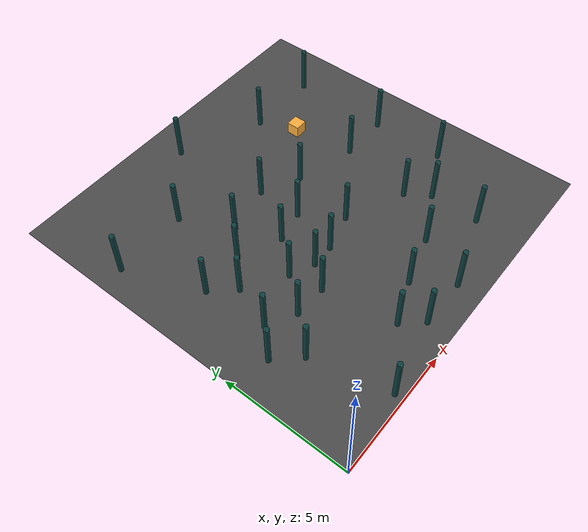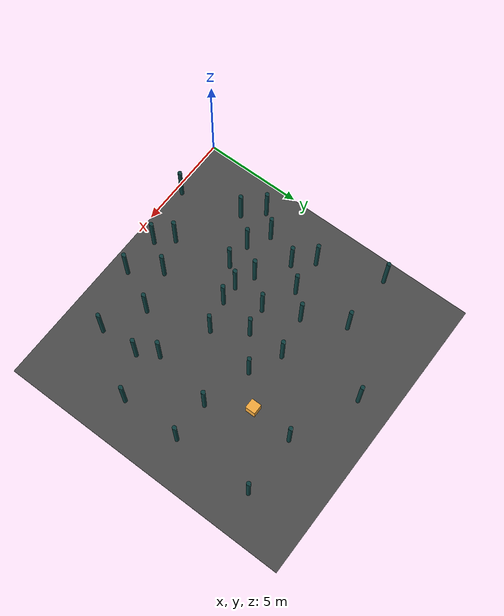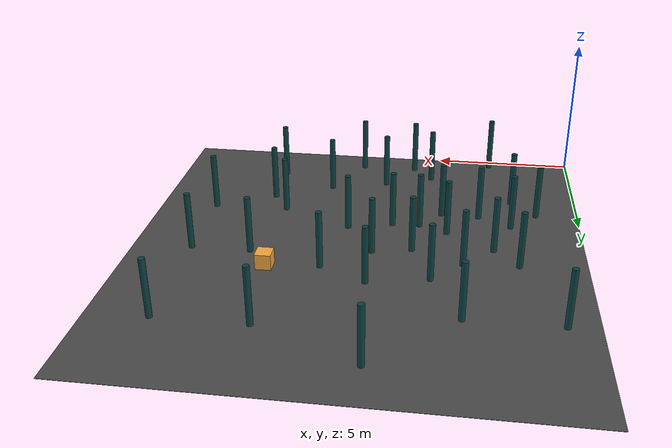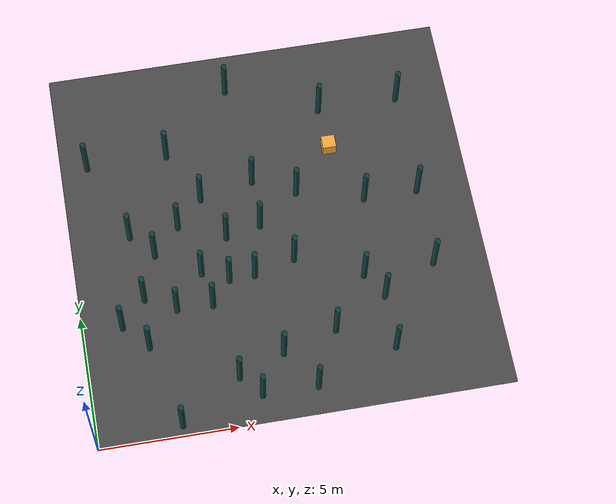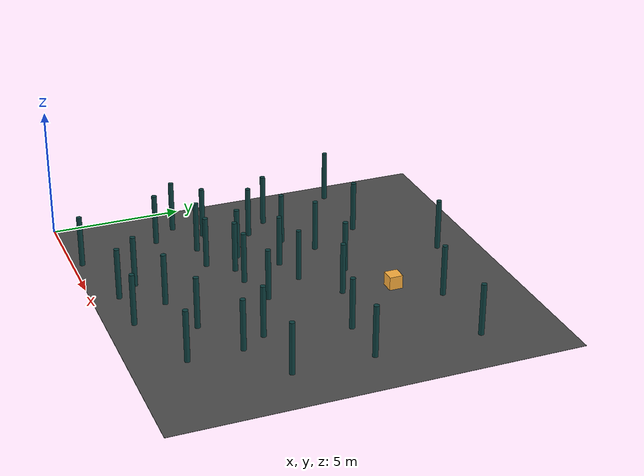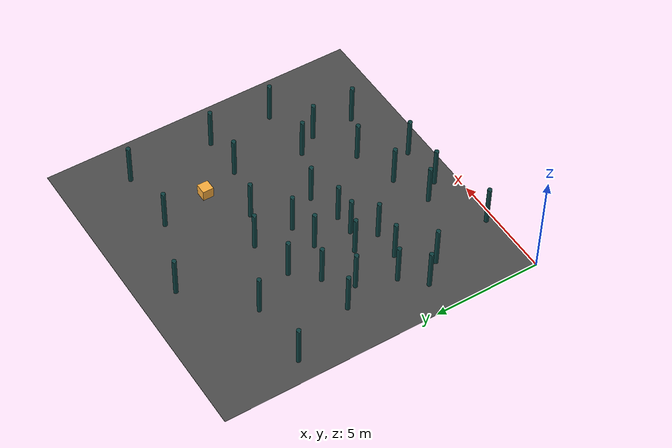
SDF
<sdf version="1.6">
 <world name="default">
  <light name="sun" type="directional">
   <pose>0 0 10 0 -0 0</pose>
   <diffuse>0.8 0.8 0.8 1</diffuse>
   <specular>0.2 0.2 0.2 1</specular>
   <attenuation>
    <range>1000</range>
    <constant>0.9</constant>
    <linear>0.01</linear>
    <quadratic>0.001</quadratic>
   </attenuation>
   <direction>-0.5 0.1 -0.9</direction>
  </light>
  <plugin name="ros_interface_plugin" filename="librotors_gazebo_ros_interface_plugin.so"/>
  <gravity>0 0 -9.8</gravity>
  <magnetic_field>6e-06 2.3e-05 -4.2e-05</magnetic_field>
  <atmosphere type="adiabatic"/>
  <physics name="default_physics" default="0" type="ode">
   <max_step_size>0.001</max_step_size>
   <real_time_factor>1</real_time_factor>
   <real_time_update_rate>1000</real_time_update_rate>
  </physics>
  <scene><ambient>0.95 0.95 0.95 1</ambient><background>1 1 1 1</background><shadows>1</shadows></scene>
  <spherical_coordinates>
   <surface_model>EARTH_WGS84</surface_model>
   <latitude_deg>0</latitude_deg>
   <longitude_deg>0</longitude_deg>
   <elevation>0</elevation>
   <heading_deg>0</heading_deg>
  </spherical_coordinates>
  <model name="env_plane">
   <link name="link">
    <inertial>
     <mass>1</mass>
     <inertia><ixx>1</ixx><ixy>0</ixy><ixz>0</ixz><iyy>1</iyy><iyz>0</iyz><izz>1</izz></inertia>
    </inertial>
    <visual name="visual">
     <cast_shadows>0</cast_shadows>
     <geometry><box><size>15 15 0.01</size></box></geometry>
     <material>
      <script>
       <uri>model://asphalt_plane/materials/scripts</uri>
       <uri>model://asphalt_plane/materials/textures</uri>
       <name>vrc/asphalt</name>
      </script>
      <shader type="pixel"><normal_map>__default__</normal_map></shader>
      <diffuse>0.7 0.7 0.7 1</diffuse>
      <ambient>0.5 0.5 0.5 1</ambient>
      <specular>0.5 0.5 0.5 1</specular>
      <emissive>0.7 0.7 0.7 1</emissive>
     </material>
    </visual>
    <collision name="collision">
     <geometry><box><size>20 20 0.1</size></box></geometry>
     <surface>
      <friction>
       <ode><mu>1</mu><mu2>1</mu2><fdir1>0 0 0</fdir1><slip1>0</slip1><slip2>0</slip2></ode>
       <torsional>
        <coefficient>1</coefficient>
        <patch_radius>0</patch_radius>
        <surface_radius>0</surface_radius>
        <use_patch_radius>1</use_patch_radius>
        <ode><slip>0</slip></ode>
       </torsional>
      </friction>
      <bounce><restitution_coefficient>0</restitution_coefficient><threshold>1e+06</threshold></bounce>
      <contact>
       <collide_without_contact>0</collide_without_contact>
       <collide_without_contact_bitmask>1</collide_without_contact_bitmask>
       <collide_bitmask>1</collide_bitmask>
       <ode>
        <soft_cfm>0</soft_cfm>
        <soft_erp>0.2</soft_erp>
        <kp>1e+13</kp>
        <kd>1</kd>
        <max_vel>0.01</max_vel>
        <min_depth>0</min_depth>
       </ode>
       <bullet>
        <split_impulse>1</split_impulse>
        <split_impulse_penetration_threshold>-0.01</split_impulse_penetration_threshold>
        <soft_cfm>0</soft_cfm>
        <soft_erp>0.2</soft_erp>
        <kp>1e+13</kp>
        <kd>1</kd>
       </bullet>
      </contact>
     </surface>
    </collision>
   </link>
   <static>1</static>
   <pose>7.5 7.5 0 0 -0 0</pose>
  </model>
  <model name="obstacle">
   <link name="link">
    <inertial>
     <mass>112.569</mass>
     <inertia><ixx>33.2512</ixx><ixy>0</ixy><ixz>0</ixz><iyy>33.2512</iyy><iyz>0</iyz><izz>0.537779</izz></inertia>
    </inertial>
    <visual name="visual">
     <geometry><cylinder><radius>0.1</radius><length>2</length></cylinder></geometry>
     <material>
      <script><name>Gazebo/Grey</name><uri>file://media/materials/scripts/gazebo.material</uri></script>
      <shader type="pixel"><normal_map>__default__</normal_map></shader>
      <ambient>0.05 0.25 0.25 1</ambient>
      <diffuse>0.3 0.3 0.3 1</diffuse>
      <specular>0.01 0.01 0.01 1</specular>
      <emissive>0.1 0.1 0.1 1</emissive>
      <lighting>1</lighting>
     </material>
    </visual>
    <collision name="collision">
     <geometry><cylinder><radius>0.097748</radius><length>1.87509</length></cylinder></geometry>
     <surface>
      <friction>
       <ode><mu>1</mu><mu2>1</mu2><fdir1>0 0 0</fdir1><slip1>0</slip1><slip2>0</slip2></ode>
       <torsional>
        <coefficient>1</coefficient>
        <patch_radius>0</patch_radius>
        <surface_radius>0</surface_radius>
        <use_patch_radius>1</use_patch_radius>
        <ode><slip>0</slip></ode>
       </torsional>
      </friction>
      <bounce><restitution_coefficient>0</restitution_coefficient><threshold>1e+06</threshold></bounce>
      <contact>
       <collide_without_contact>0</collide_without_contact>
       <collide_without_contact_bitmask>1</collide_without_contact_bitmask>
       <collide_bitmask>1</collide_bitmask>
       <ode>
        <soft_cfm>0</soft_cfm>
        <soft_erp>0.2</soft_erp>
        <kp>1e+13</kp>
        <kd>1</kd>
        <max_vel>0.01</max_vel>
        <min_depth>0</min_depth>
       </ode>
       <bullet>
        <split_impulse>1</split_impulse>
        <split_impulse_penetration_threshold>-0.01</split_impulse_penetration_threshold>
        <soft_cfm>0</soft_cfm>
        <soft_erp>0.2</soft_erp>
        <kp>1e+13</kp>
        <kd>1</kd>
       </bullet>
      </contact>
     </surface>
    </collision>
   </link>
   <static>0</static>
   <pose>6.48526 5.60754 0.987551 -5.8e-05 3e-05 0.00436</pose>
  </model>
  <model name="obstacle_clone">
   <link name="link">
    <inertial>
     <mass>112.569</mass>
     <inertia><ixx>33.2512</ixx><ixy>0</ixy><ixz>0</ixz><iyy>33.2512</iyy><iyz>0</iyz><izz>0.537779</izz></inertia>
    </inertial>
    <visual name="visual">
     <geometry><cylinder><radius>0.1</radius><length>2</length></cylinder></geometry>
     <material>
      <script><name>Gazebo/Grey</name><uri>file://media/materials/scripts/gazebo.material</uri></script>
      <shader type="pixel"><normal_map>__default__</normal_map></shader>
      <ambient>0.05 0.25 0.25 1</ambient>
      <diffuse>0.3 0.3 0.3 1</diffuse>
      <specular>0.01 0.01 0.01 1</specular>
      <emissive>0.1 0.1 0.1 1</emissive>
      <lighting>1</lighting>
     </material>
    </visual>
    <collision name="collision">
     <geometry><cylinder><radius>0.097748</radius><length>1.87509</length></cylinder></geometry>
     <surface>
      <friction>
       <ode><mu>1</mu><mu2>1</mu2><fdir1>0 0 0</fdir1><slip1>0</slip1><slip2>0</slip2></ode>
       <torsional>
        <coefficient>1</coefficient>
        <patch_radius>0</patch_radius>
        <surface_radius>0</surface_radius>
        <use_patch_radius>1</use_patch_radius>
        <ode><slip>0</slip></ode>
       </torsional>
      </friction>
      <bounce><restitution_coefficient>0</restitution_coefficient><threshold>1e+06</threshold></bounce>
      <contact>
       <collide_without_contact>0</collide_without_contact>
       <collide_without_contact_bitmask>1</collide_without_contact_bitmask>
       <collide_bitmask>1</collide_bitmask>
       <ode>
        <soft_cfm>0</soft_cfm>
        <soft_erp>0.2</soft_erp>
        <kp>1e+13</kp>
        <kd>1</kd>
        <max_vel>0.01</max_vel>
        <min_depth>0</min_depth>
       </ode>
       <bullet>
        <split_impulse>1</split_impulse>
        <split_impulse_penetration_threshold>-0.01</split_impulse_penetration_threshold>
        <soft_cfm>0</soft_cfm>
        <soft_erp>0.2</soft_erp>
        <kp>1e+13</kp>
        <kd>1</kd>
       </bullet>
      </contact>
     </surface>
    </collision>
   </link>
   <static>0</static>
   <pose>1.45905 4.37795 0.987544 -3.5e-05 8e-06 0.003637</pose>
  </model>
  <model name="obstacle_clone_0">
   <link name="link">
    <inertial>
     <mass>112.569</mass>
     <inertia><ixx>33.2512</ixx><ixy>0</ixy><ixz>0</ixz><iyy>33.2512</iyy><iyz>0</iyz><izz>0.537779</izz></inertia>
    </inertial>
    <visual name="visual">
     <geometry><cylinder><radius>0.1</radius><length>2</length></cylinder></geometry>
     <material>
      <script><name>Gazebo/Grey</name><uri>file://media/materials/scripts/gazebo.material</uri></script>
      <shader type="pixel"><normal_map>__default__</normal_map></shader>
      <ambient>0.05 0.25 0.25 1</ambient>
      <diffuse>0.3 0.3 0.3 1</diffuse>
      <specular>0.01 0.01 0.01 1</specular>
      <emissive>0.1 0.1 0.1 1</emissive>
      <lighting>1</lighting>
     </material>
    </visual>
    <collision name="collision">
     <geometry><cylinder><radius>0.097748</radius><length>1.87509</length></cylinder></geometry>
     <surface>
      <friction>
       <ode><mu>1</mu><mu2>1</mu2><fdir1>0 0 0</fdir1><slip1>0</slip1><slip2>0</slip2></ode>
       <torsional>
        <coefficient>1</coefficient>
        <patch_radius>0</patch_radius>
        <surface_radius>0</surface_radius>
        <use_patch_radius>1</use_patch_radius>
        <ode><slip>0</slip></ode>
       </torsional>
      </friction>
      <bounce><restitution_coefficient>0</restitution_coefficient><threshold>1e+06</threshold></bounce>
      <contact>
       <collide_without_contact>0</collide_without_contact>
       <collide_without_contact_bitmask>1</collide_without_contact_bitmask>
       <collide_bitmask>1</collide_bitmask>
       <ode>
        <soft_cfm>0</soft_cfm>
        <soft_erp>0.2</soft_erp>
        <kp>1e+13</kp>
        <kd>1</kd>
        <max_vel>0.01</max_vel>
        <min_depth>0</min_depth>
       </ode>
       <bullet>
        <split_impulse>1</split_impulse>
        <split_impulse_penetration_threshold>-0.01</split_impulse_penetration_threshold>
        <soft_cfm>0</soft_cfm>
        <soft_erp>0.2</soft_erp>
        <kp>1e+13</kp>
        <kd>1</kd>
       </bullet>
      </contact>
     </surface>
    </collision>
   </link>
   <static>0</static>
   <pose>3.49251 4.73719 0.987541 -5.7e-05 2.6e-05 0.006761</pose>
  </model>
  <model name="obstacle_clone_1">
   <link name="link">
    <inertial>
     <mass>112.569</mass>
     <inertia><ixx>33.2512</ixx><ixy>0</ixy><ixz>0</ixz><iyy>33.2512</iyy><iyz>0</iyz><izz>0.537779</izz></inertia>
    </inertial>
    <visual name="visual">
     <geometry><cylinder><radius>0.1</radius><length>2</length></cylinder></geometry>
     <material>
      <script><name>Gazebo/Grey</name><uri>file://media/materials/scripts/gazebo.material</uri></script>
      <shader type="pixel"><normal_map>__default__</normal_map></shader>
      <ambient>0.05 0.25 0.25 1</ambient>
      <diffuse>0.3 0.3 0.3 1</diffuse>
      <specular>0.01 0.01 0.01 1</specular>
      <emissive>0.1 0.1 0.1 1</emissive>
      <lighting>1</lighting>
     </material>
    </visual>
    <collision name="collision">
     <geometry><cylinder><radius>0.097748</radius><length>1.87509</length></cylinder></geometry>
     <surface>
      <friction>
       <ode><mu>1</mu><mu2>1</mu2><fdir1>0 0 0</fdir1><slip1>0</slip1><slip2>0</slip2></ode>
       <torsional>
        <coefficient>1</coefficient>
        <patch_radius>0</patch_radius>
        <surface_radius>0</surface_radius>
        <use_patch_radius>1</use_patch_radius>
        <ode><slip>0</slip></ode>
       </torsional>
      </friction>
      <bounce><restitution_coefficient>0</restitution_coefficient><threshold>1e+06</threshold></bounce>
      <contact>
       <collide_without_contact>0</collide_without_contact>
       <collide_without_contact_bitmask>1</collide_without_contact_bitmask>
       <collide_bitmask>1</collide_bitmask>
       <ode>
        <soft_cfm>0</soft_cfm>
        <soft_erp>0.2</soft_erp>
        <kp>1e+13</kp>
        <kd>1</kd>
        <max_vel>0.01</max_vel>
        <min_depth>0</min_depth>
       </ode>
       <bullet>
        <split_impulse>1</split_impulse>
        <split_impulse_penetration_threshold>-0.01</split_impulse_penetration_threshold>
        <soft_cfm>0</soft_cfm>
        <soft_erp>0.2</soft_erp>
        <kp>1e+13</kp>
        <kd>1</kd>
       </bullet>
      </contact>
     </surface>
    </collision>
   </link>
   <static>0</static>
   <pose>5.30401 1.78357 0.987542 -6e-05 2.8e-05 0.006723</pose>
  </model>
  <model name="obstacle_clone_2">
   <link name="link">
    <inertial>
     <mass>112.569</mass>
     <inertia><ixx>33.2512</ixx><ixy>0</ixy><ixz>0</ixz><iyy>33.2512</iyy><iyz>0</iyz><izz>0.537779</izz></inertia>
    </inertial>
    <visual name="visual">
     <geometry><cylinder><radius>0.1</radius><length>2</length></cylinder></geometry>
     <material>
      <script><name>Gazebo/Grey</name><uri>file://media/materials/scripts/gazebo.material</uri></script>
      <shader type="pixel"><normal_map>__default__</normal_map></shader>
      <ambient>0.05 0.25 0.25 1</ambient>
      <diffuse>0.3 0.3 0.3 1</diffuse>
      <specular>0.01 0.01 0.01 1</specular>
      <emissive>0.1 0.1 0.1 1</emissive>
      <lighting>1</lighting>
     </material>
    </visual>
    <collision name="collision">
     <geometry><cylinder><radius>0.097748</radius><length>1.87509</length></cylinder></geometry>
     <surface>
      <friction>
       <ode><mu>1</mu><mu2>1</mu2><fdir1>0 0 0</fdir1><slip1>0</slip1><slip2>0</slip2></ode>
       <torsional>
        <coefficient>1</coefficient>
        <patch_radius>0</patch_radius>
        <surface_radius>0</surface_radius>
        <use_patch_radius>1</use_patch_radius>
        <ode><slip>0</slip></ode>
       </torsional>
      </friction>
      <bounce><restitution_coefficient>0</restitution_coefficient><threshold>1e+06</threshold></bounce>
      <contact>
       <collide_without_contact>0</collide_without_contact>
       <collide_without_contact_bitmask>1</collide_without_contact_bitmask>
       <collide_bitmask>1</collide_bitmask>
       <ode>
        <soft_cfm>0</soft_cfm>
        <soft_erp>0.2</soft_erp>
        <kp>1e+13</kp>
        <kd>1</kd>
        <max_vel>0.01</max_vel>
        <min_depth>0</min_depth>
       </ode>
       <bullet>
        <split_impulse>1</split_impulse>
        <split_impulse_penetration_threshold>-0.01</split_impulse_penetration_threshold>
        <soft_cfm>0</soft_cfm>
        <soft_erp>0.2</soft_erp>
        <kp>1e+13</kp>
        <kd>1</kd>
       </bullet>
      </contact>
     </surface>
    </collision>
   </link>
   <static>0</static>
   <pose>2.19392 7.89594 0.987542 -5.7e-05 2.8e-05 0.005702</pose>
  </model>
  <model name="obstacle_clone_3">
   <link name="link">
    <inertial>
     <mass>112.569</mass>
     <inertia><ixx>33.2512</ixx><ixy>0</ixy><ixz>0</ixz><iyy>33.2512</iyy><iyz>0</iyz><izz>0.537779</izz></inertia>
    </inertial>
    <visual name="visual">
     <geometry><cylinder><radius>0.1</radius><length>2</length></cylinder></geometry>
     <material>
      <script><name>Gazebo/Grey</name><uri>file://media/materials/scripts/gazebo.material</uri></script>
      <shader type="pixel"><normal_map>__default__</normal_map></shader>
      <ambient>0.05 0.25 0.25 1</ambient>
      <diffuse>0.3 0.3 0.3 1</diffuse>
      <specular>0.01 0.01 0.01 1</specular>
      <emissive>0.1 0.1 0.1 1</emissive>
      <lighting>1</lighting>
     </material>
    </visual>
    <collision name="collision">
     <geometry><cylinder><radius>0.097748</radius><length>1.87509</length></cylinder></geometry>
     <surface>
      <friction>
       <ode><mu>1</mu><mu2>1</mu2><fdir1>0 0 0</fdir1><slip1>0</slip1><slip2>0</slip2></ode>
       <torsional>
        <coefficient>1</coefficient>
        <patch_radius>0</patch_radius>
        <surface_radius>0</surface_radius>
        <use_patch_radius>1</use_patch_radius>
        <ode><slip>0</slip></ode>
       </torsional>
      </friction>
      <bounce><restitution_coefficient>0</restitution_coefficient><threshold>1e+06</threshold></bounce>
      <contact>
       <collide_without_contact>0</collide_without_contact>
       <collide_without_contact_bitmask>1</collide_without_contact_bitmask>
       <collide_bitmask>1</collide_bitmask>
       <ode>
        <soft_cfm>0</soft_cfm>
        <soft_erp>0.2</soft_erp>
        <kp>1e+13</kp>
        <kd>1</kd>
        <max_vel>0.01</max_vel>
        <min_depth>0</min_depth>
       </ode>
       <bullet>
        <split_impulse>1</split_impulse>
        <split_impulse_penetration_threshold>-0.01</split_impulse_penetration_threshold>
        <soft_cfm>0</soft_cfm>
        <soft_erp>0.2</soft_erp>
        <kp>1e+13</kp>
        <kd>1</kd>
       </bullet>
      </contact>
     </surface>
    </collision>
   </link>
   <static>0</static>
   <pose>1.00014 11.0001 0.987542 -5.8e-05 2.7e-05 0.00418</pose>
  </model>
  <model name="obstacle_clone_4">
   <link name="link">
    <inertial>
     <mass>112.569</mass>
     <inertia><ixx>33.2512</ixx><ixy>0</ixy><ixz>0</ixz><iyy>33.2512</iyy><iyz>0</iyz><izz>0.537779</izz></inertia>
    </inertial>
    <visual name="visual">
     <geometry><cylinder><radius>0.1</radius><length>2</length></cylinder></geometry>
     <material>
      <script><name>Gazebo/Grey</name><uri>file://media/materials/scripts/gazebo.material</uri></script>
      <shader type="pixel"><normal_map>__default__</normal_map></shader>
      <ambient>0.05 0.25 0.25 1</ambient>
      <diffuse>0.3 0.3 0.3 1</diffuse>
      <specular>0.01 0.01 0.01 1</specular>
      <emissive>0.1 0.1 0.1 1</emissive>
      <lighting>1</lighting>
     </material>
    </visual>
    <collision name="collision">
     <geometry><cylinder><radius>0.097748</radius><length>1.87509</length></cylinder></geometry>
     <surface>
      <friction>
       <ode><mu>1</mu><mu2>1</mu2><fdir1>0 0 0</fdir1><slip1>0</slip1><slip2>0</slip2></ode>
       <torsional>
        <coefficient>1</coefficient>
        <patch_radius>0</patch_radius>
        <surface_radius>0</surface_radius>
        <use_patch_radius>1</use_patch_radius>
        <ode><slip>0</slip></ode>
       </torsional>
      </friction>
      <bounce><restitution_coefficient>0</restitution_coefficient><threshold>1e+06</threshold></bounce>
      <contact>
       <collide_without_contact>0</collide_without_contact>
       <collide_without_contact_bitmask>1</collide_without_contact_bitmask>
       <collide_bitmask>1</collide_bitmask>
       <ode>
        <soft_cfm>0</soft_cfm>
        <soft_erp>0.2</soft_erp>
        <kp>1e+13</kp>
        <kd>1</kd>
        <max_vel>0.01</max_vel>
        <min_depth>0</min_depth>
       </ode>
       <bullet>
        <split_impulse>1</split_impulse>
        <split_impulse_penetration_threshold>-0.01</split_impulse_penetration_threshold>
        <soft_cfm>0</soft_cfm>
        <soft_erp>0.2</soft_erp>
        <kp>1e+13</kp>
        <kd>1</kd>
       </bullet>
      </contact>
     </surface>
    </collision>
   </link>
   <static>0</static>
   <pose>7.00036 2.43391 0.987542 -5.6e-05 2.9e-05 0.006587</pose>
  </model>
  <model name="obstacle_clone_5">
   <link name="link">
    <inertial>
     <mass>112.569</mass>
     <inertia><ixx>33.2512</ixx><ixy>0</ixy><ixz>0</ixz><iyy>33.2512</iyy><iyz>0</iyz><izz>0.537779</izz></inertia>
    </inertial>
    <visual name="visual">
     <geometry><cylinder><radius>0.1</radius><length>2</length></cylinder></geometry>
     <material>
      <script><name>Gazebo/Grey</name><uri>file://media/materials/scripts/gazebo.material</uri></script>
      <shader type="pixel"><normal_map>__default__</normal_map></shader>
      <ambient>0.05 0.25 0.25 1</ambient>
      <diffuse>0.3 0.3 0.3 1</diffuse>
      <specular>0.01 0.01 0.01 1</specular>
      <emissive>0.1 0.1 0.1 1</emissive>
      <lighting>1</lighting>
     </material>
    </visual>
    <collision name="collision">
     <geometry><cylinder><radius>0.097748</radius><length>1.87509</length></cylinder></geometry>
     <surface>
      <friction>
       <ode><mu>1</mu><mu2>1</mu2><fdir1>0 0 0</fdir1><slip1>0</slip1><slip2>0</slip2></ode>
       <torsional>
        <coefficient>1</coefficient>
        <patch_radius>0</patch_radius>
        <surface_radius>0</surface_radius>
        <use_patch_radius>1</use_patch_radius>
        <ode><slip>0</slip></ode>
       </torsional>
      </friction>
      <bounce><restitution_coefficient>0</restitution_coefficient><threshold>1e+06</threshold></bounce>
      <contact>
       <collide_without_contact>0</collide_without_contact>
       <collide_without_contact_bitmask>1</collide_without_contact_bitmask>
       <collide_bitmask>1</collide_bitmask>
       <ode>
        <soft_cfm>0</soft_cfm>
        <soft_erp>0.2</soft_erp>
        <kp>1e+13</kp>
        <kd>1</kd>
        <max_vel>0.01</max_vel>
        <min_depth>0</min_depth>
       </ode>
       <bullet>
        <split_impulse>1</split_impulse>
        <split_impulse_penetration_threshold>-0.01</split_impulse_penetration_threshold>
        <soft_cfm>0</soft_cfm>
        <soft_erp>0.2</soft_erp>
        <kp>1e+13</kp>
        <kd>1</kd>
       </bullet>
      </contact>
     </surface>
    </collision>
   </link>
   <static>0</static>
   <pose>5.00035 9.00007 0.987551 -6.2e-05 2.7e-05 0.006645</pose>
  </model>
  <model name="obstacle_clone_6">
   <link name="link">
    <inertial>
     <mass>112.569</mass>
     <inertia><ixx>33.2512</ixx><ixy>0</ixy><ixz>0</ixz><iyy>33.2512</iyy><iyz>0</iyz><izz>0.537779</izz></inertia>
    </inertial>
    <visual name="visual">
     <geometry><cylinder><radius>0.1</radius><length>2</length></cylinder></geometry>
     <material>
      <script><name>Gazebo/Grey</name><uri>file://media/materials/scripts/gazebo.material</uri></script>
      <shader type="pixel"><normal_map>__default__</normal_map></shader>
      <ambient>0.05 0.25 0.25 1</ambient>
      <diffuse>0.3 0.3 0.3 1</diffuse>
      <specular>0.01 0.01 0.01 1</specular>
      <emissive>0.1 0.1 0.1 1</emissive>
      <lighting>1</lighting>
     </material>
    </visual>
    <collision name="collision">
     <geometry><cylinder><radius>0.097748</radius><length>1.87509</length></cylinder></geometry>
     <surface>
      <friction>
       <ode><mu>1</mu><mu2>1</mu2><fdir1>0 0 0</fdir1><slip1>0</slip1><slip2>0</slip2></ode>
       <torsional>
        <coefficient>1</coefficient>
        <patch_radius>0</patch_radius>
        <surface_radius>0</surface_radius>
        <use_patch_radius>1</use_patch_radius>
        <ode><slip>0</slip></ode>
       </torsional>
      </friction>
      <bounce><restitution_coefficient>0</restitution_coefficient><threshold>1e+06</threshold></bounce>
      <contact>
       <collide_without_contact>0</collide_without_contact>
       <collide_without_contact_bitmask>1</collide_without_contact_bitmask>
       <collide_bitmask>1</collide_bitmask>
       <ode>
        <soft_cfm>0</soft_cfm>
        <soft_erp>0.2</soft_erp>
        <kp>1e+13</kp>
        <kd>1</kd>
        <max_vel>0.01</max_vel>
        <min_depth>0</min_depth>
       </ode>
       <bullet>
        <split_impulse>1</split_impulse>
        <split_impulse_penetration_threshold>-0.01</split_impulse_penetration_threshold>
        <soft_cfm>0</soft_cfm>
        <soft_erp>0.2</soft_erp>
        <kp>1e+13</kp>
        <kd>1</kd>
       </bullet>
      </contact>
     </surface>
    </collision>
   </link>
   <static>0</static>
   <pose>4.00036 8.00005 0.987541 -5.6e-05 2.7e-05 0.006554</pose>
  </model>
  <model name="obstacle_clone_7">
   <link name="link">
    <inertial>
     <mass>112.569</mass>
     <inertia><ixx>33.2512</ixx><ixy>0</ixy><ixz>0</ixz><iyy>33.2512</iyy><iyz>0</iyz><izz>0.537779</izz></inertia>
    </inertial>
    <visual name="visual">
     <geometry><cylinder><radius>0.1</radius><length>2</length></cylinder></geometry>
     <material>
      <script><name>Gazebo/Grey</name><uri>file://media/materials/scripts/gazebo.material</uri></script>
      <shader type="pixel"><normal_map>__default__</normal_map></shader>
      <ambient>0.05 0.25 0.25 1</ambient>
      <diffuse>0.3 0.3 0.3 1</diffuse>
      <specular>0.01 0.01 0.01 1</specular>
      <emissive>0.1 0.1 0.1 1</emissive>
      <lighting>1</lighting>
     </material>
    </visual>
    <collision name="collision">
     <geometry><cylinder><radius>0.097748</radius><length>1.87509</length></cylinder></geometry>
     <surface>
      <friction>
       <ode><mu>1</mu><mu2>1</mu2><fdir1>0 0 0</fdir1><slip1>0</slip1><slip2>0</slip2></ode>
       <torsional>
        <coefficient>1</coefficient>
        <patch_radius>0</patch_radius>
        <surface_radius>0</surface_radius>
        <use_patch_radius>1</use_patch_radius>
        <ode><slip>0</slip></ode>
       </torsional>
      </friction>
      <bounce><restitution_coefficient>0</restitution_coefficient><threshold>1e+06</threshold></bounce>
      <contact>
       <collide_without_contact>0</collide_without_contact>
       <collide_without_contact_bitmask>1</collide_without_contact_bitmask>
       <collide_bitmask>1</collide_bitmask>
       <ode>
        <soft_cfm>0</soft_cfm>
        <soft_erp>0.2</soft_erp>
        <kp>1e+13</kp>
        <kd>1</kd>
        <max_vel>0.01</max_vel>
        <min_depth>0</min_depth>
       </ode>
       <bullet>
        <split_impulse>1</split_impulse>
        <split_impulse_penetration_threshold>-0.01</split_impulse_penetration_threshold>
        <soft_cfm>0</soft_cfm>
        <soft_erp>0.2</soft_erp>
        <kp>1e+13</kp>
        <kd>1</kd>
       </bullet>
      </contact>
     </surface>
    </collision>
   </link>
   <static>0</static>
   <pose>2.31368 3.4611 0.987545 -2.9e-05 -4.3e-05 0.004628</pose>
  </model>
  <model name="obstacle_clone_8">
   <link name="link">
    <inertial>
     <mass>112.569</mass>
     <inertia><ixx>33.2512</ixx><ixy>0</ixy><ixz>0</ixz><iyy>33.2512</iyy><iyz>0</iyz><izz>0.537779</izz></inertia>
    </inertial>
    <visual name="visual">
     <geometry><cylinder><radius>0.1</radius><length>2</length></cylinder></geometry>
     <material>
      <script><name>Gazebo/Grey</name><uri>file://media/materials/scripts/gazebo.material</uri></script>
      <shader type="pixel"><normal_map>__default__</normal_map></shader>
      <ambient>0.05 0.25 0.25 1</ambient>
      <diffuse>0.3 0.3 0.3 1</diffuse>
      <specular>0.01 0.01 0.01 1</specular>
      <emissive>0.1 0.1 0.1 1</emissive>
      <lighting>1</lighting>
     </material>
    </visual>
    <collision name="collision">
     <geometry><cylinder><radius>0.097748</radius><length>1.87509</length></cylinder></geometry>
     <surface>
      <friction>
       <ode><mu>1</mu><mu2>1</mu2><fdir1>0 0 0</fdir1><slip1>0</slip1><slip2>0</slip2></ode>
       <torsional>
        <coefficient>1</coefficient>
        <patch_radius>0</patch_radius>
        <surface_radius>0</surface_radius>
        <use_patch_radius>1</use_patch_radius>
        <ode><slip>0</slip></ode>
       </torsional>
      </friction>
      <bounce><restitution_coefficient>0</restitution_coefficient><threshold>1e+06</threshold></bounce>
      <contact>
       <collide_without_contact>0</collide_without_contact>
       <collide_without_contact_bitmask>1</collide_without_contact_bitmask>
       <collide_bitmask>1</collide_bitmask>
       <ode>
        <soft_cfm>0</soft_cfm>
        <soft_erp>0.2</soft_erp>
        <kp>1e+13</kp>
        <kd>1</kd>
        <max_vel>0.01</max_vel>
        <min_depth>0</min_depth>
       </ode>
       <bullet>
        <split_impulse>1</split_impulse>
        <split_impulse_penetration_threshold>-0.01</split_impulse_penetration_threshold>
        <soft_cfm>0</soft_cfm>
        <soft_erp>0.2</soft_erp>
        <kp>1e+13</kp>
        <kd>1</kd>
       </bullet>
      </contact>
     </surface>
    </collision>
   </link>
   <static>0</static>
   <pose>7.00036 9.40157 0.987551 -5.5e-05 2.6e-05 0.006663</pose>
  </model>
  <model name="obstacle_clone_9">
   <link name="link">
    <inertial>
     <mass>112.569</mass>
     <inertia><ixx>33.2512</ixx><ixy>0</ixy><ixz>0</ixz><iyy>33.2512</iyy><iyz>0</iyz><izz>0.537779</izz></inertia>
    </inertial>
    <visual name="visual">
     <geometry><cylinder><radius>0.1</radius><length>2</length></cylinder></geometry>
     <material>
      <script><name>Gazebo/Grey</name><uri>file://media/materials/scripts/gazebo.material</uri></script>
      <shader type="pixel"><normal_map>__default__</normal_map></shader>
      <ambient>0.05 0.25 0.25 1</ambient>
      <diffuse>0.3 0.3 0.3 1</diffuse>
      <specular>0.01 0.01 0.01 1</specular>
      <emissive>0.1 0.1 0.1 1</emissive>
      <lighting>1</lighting>
     </material>
    </visual>
    <collision name="collision">
     <geometry><cylinder><radius>0.097748</radius><length>1.87509</length></cylinder></geometry>
     <surface>
      <friction>
       <ode><mu>1</mu><mu2>1</mu2><fdir1>0 0 0</fdir1><slip1>0</slip1><slip2>0</slip2></ode>
       <torsional>
        <coefficient>1</coefficient>
        <patch_radius>0</patch_radius>
        <surface_radius>0</surface_radius>
        <use_patch_radius>1</use_patch_radius>
        <ode><slip>0</slip></ode>
       </torsional>
      </friction>
      <bounce><restitution_coefficient>0</restitution_coefficient><threshold>1e+06</threshold></bounce>
      <contact>
       <collide_without_contact>0</collide_without_contact>
       <collide_without_contact_bitmask>1</collide_without_contact_bitmask>
       <collide_bitmask>1</collide_bitmask>
       <ode>
        <soft_cfm>0</soft_cfm>
        <soft_erp>0.2</soft_erp>
        <kp>1e+13</kp>
        <kd>1</kd>
        <max_vel>0.01</max_vel>
        <min_depth>0</min_depth>
       </ode>
       <bullet>
        <split_impulse>1</split_impulse>
        <split_impulse_penetration_threshold>-0.01</split_impulse_penetration_threshold>
        <soft_cfm>0</soft_cfm>
        <soft_erp>0.2</soft_erp>
        <kp>1e+13</kp>
        <kd>1</kd>
       </bullet>
      </contact>
     </surface>
    </collision>
   </link>
   <static>0</static>
   <pose>5.69881 7.28333 0.987551 -5.5e-05 2.5e-05 0.006572</pose>
  </model>
  <model name="obstacle_clone_10">
   <link name="link">
    <inertial>
     <mass>112.569</mass>
     <inertia><ixx>33.2512</ixx><ixy>0</ixy><ixz>0</ixz><iyy>33.2512</iyy><iyz>0</iyz><izz>0.537779</izz></inertia>
    </inertial>
    <visual name="visual">
     <geometry><cylinder><radius>0.1</radius><length>2</length></cylinder></geometry>
     <material>
      <script><name>Gazebo/Grey</name><uri>file://media/materials/scripts/gazebo.material</uri></script>
      <shader type="pixel"><normal_map>__default__</normal_map></shader>
      <ambient>0.05 0.25 0.25 1</ambient>
      <diffuse>0.3 0.3 0.3 1</diffuse>
      <specular>0.01 0.01 0.01 1</specular>
      <emissive>0.1 0.1 0.1 1</emissive>
      <lighting>1</lighting>
     </material>
    </visual>
    <collision name="collision">
     <geometry><cylinder><radius>0.097748</radius><length>1.87509</length></cylinder></geometry>
     <surface>
      <friction>
       <ode><mu>1</mu><mu2>1</mu2><fdir1>0 0 0</fdir1><slip1>0</slip1><slip2>0</slip2></ode>
       <torsional>
        <coefficient>1</coefficient>
        <patch_radius>0</patch_radius>
        <surface_radius>0</surface_radius>
        <use_patch_radius>1</use_patch_radius>
        <ode><slip>0</slip></ode>
       </torsional>
      </friction>
      <bounce><restitution_coefficient>0</restitution_coefficient><threshold>1e+06</threshold></bounce>
      <contact>
       <collide_without_contact>0</collide_without_contact>
       <collide_without_contact_bitmask>1</collide_without_contact_bitmask>
       <collide_bitmask>1</collide_bitmask>
       <ode>
        <soft_cfm>0</soft_cfm>
        <soft_erp>0.2</soft_erp>
        <kp>1e+13</kp>
        <kd>1</kd>
        <max_vel>0.01</max_vel>
        <min_depth>0</min_depth>
       </ode>
       <bullet>
        <split_impulse>1</split_impulse>
        <split_impulse_penetration_threshold>-0.01</split_impulse_penetration_threshold>
        <soft_cfm>0</soft_cfm>
        <soft_erp>0.2</soft_erp>
        <kp>1e+13</kp>
        <kd>1</kd>
       </bullet>
      </contact>
     </surface>
    </collision>
   </link>
   <static>0</static>
   <pose>4.58014 6.00004 0.987543 -3e-05 1.3e-05 0.00599</pose>
  </model>
  <model name="obstacle_clone_11">
   <link name="link">
    <inertial>
     <mass>112.569</mass>
     <inertia><ixx>33.2512</ixx><ixy>0</ixy><ixz>0</ixz><iyy>33.2512</iyy><iyz>0</iyz><izz>0.537779</izz></inertia>
    </inertial>
    <visual name="visual">
     <geometry><cylinder><radius>0.1</radius><length>2</length></cylinder></geometry>
     <material>
      <script><name>Gazebo/Grey</name><uri>file://media/materials/scripts/gazebo.material</uri></script>
      <shader type="pixel"><normal_map>__default__</normal_map></shader>
      <ambient>0.05 0.25 0.25 1</ambient>
      <diffuse>0.3 0.3 0.3 1</diffuse>
      <specular>0.01 0.01 0.01 1</specular>
      <emissive>0.1 0.1 0.1 1</emissive>
      <lighting>1</lighting>
     </material>
    </visual>
    <collision name="collision">
     <geometry><cylinder><radius>0.097748</radius><length>1.87509</length></cylinder></geometry>
     <surface>
      <friction>
       <ode><mu>1</mu><mu2>1</mu2><fdir1>0 0 0</fdir1><slip1>0</slip1><slip2>0</slip2></ode>
       <torsional>
        <coefficient>1</coefficient>
        <patch_radius>0</patch_radius>
        <surface_radius>0</surface_radius>
        <use_patch_radius>1</use_patch_radius>
        <ode><slip>0</slip></ode>
       </torsional>
      </friction>
      <bounce><restitution_coefficient>0</restitution_coefficient><threshold>1e+06</threshold></bounce>
      <contact>
       <collide_without_contact>0</collide_without_contact>
       <collide_without_contact_bitmask>1</collide_without_contact_bitmask>
       <collide_bitmask>1</collide_bitmask>
       <ode>
        <soft_cfm>0</soft_cfm>
        <soft_erp>0.2</soft_erp>
        <kp>1e+13</kp>
        <kd>1</kd>
        <max_vel>0.01</max_vel>
        <min_depth>0</min_depth>
       </ode>
       <bullet>
        <split_impulse>1</split_impulse>
        <split_impulse_penetration_threshold>-0.01</split_impulse_penetration_threshold>
        <soft_cfm>0</soft_cfm>
        <soft_erp>0.2</soft_erp>
        <kp>1e+13</kp>
        <kd>1</kd>
       </bullet>
      </contact>
     </surface>
    </collision>
   </link>
   <static>0</static>
   <pose>9.00035 3.00008 0.987542 -6.3e-05 2.8e-05 0.006623</pose>
  </model>
  <model name="obstacle_clone_12">
   <link name="link">
    <inertial>
     <mass>112.569</mass>
     <inertia><ixx>33.2512</ixx><ixy>0</ixy><ixz>0</ixz><iyy>33.2512</iyy><iyz>0</iyz><izz>0.537779</izz></inertia>
    </inertial>
    <visual name="visual">
     <geometry><cylinder><radius>0.1</radius><length>2</length></cylinder></geometry>
     <material>
      <script><name>Gazebo/Grey</name><uri>file://media/materials/scripts/gazebo.material</uri></script>
      <shader type="pixel"><normal_map>__default__</normal_map></shader>
      <ambient>0.05 0.25 0.25 1</ambient>
      <diffuse>0.3 0.3 0.3 1</diffuse>
      <specular>0.01 0.01 0.01 1</specular>
      <emissive>0.1 0.1 0.1 1</emissive>
      <lighting>1</lighting>
     </material>
    </visual>
    <collision name="collision">
     <geometry><cylinder><radius>0.097748</radius><length>1.87509</length></cylinder></geometry>
     <surface>
      <friction>
       <ode><mu>1</mu><mu2>1</mu2><fdir1>0 0 0</fdir1><slip1>0</slip1><slip2>0</slip2></ode>
       <torsional>
        <coefficient>1</coefficient>
        <patch_radius>0</patch_radius>
        <surface_radius>0</surface_radius>
        <use_patch_radius>1</use_patch_radius>
        <ode><slip>0</slip></ode>
       </torsional>
      </friction>
      <bounce><restitution_coefficient>0</restitution_coefficient><threshold>1e+06</threshold></bounce>
      <contact>
       <collide_without_contact>0</collide_without_contact>
       <collide_without_contact_bitmask>1</collide_without_contact_bitmask>
       <collide_bitmask>1</collide_bitmask>
       <ode>
        <soft_cfm>0</soft_cfm>
        <soft_erp>0.2</soft_erp>
        <kp>1e+13</kp>
        <kd>1</kd>
        <max_vel>0.01</max_vel>
        <min_depth>0</min_depth>
       </ode>
       <bullet>
        <split_impulse>1</split_impulse>
        <split_impulse_penetration_threshold>-0.01</split_impulse_penetration_threshold>
        <soft_cfm>0</soft_cfm>
        <soft_erp>0.2</soft_erp>
        <kp>1e+13</kp>
        <kd>1</kd>
       </bullet>
      </contact>
     </surface>
    </collision>
   </link>
   <static>0</static>
   <pose>8.55034 8.6666 0.987551 -5.7e-05 2.6e-05 0.006613</pose>
  </model>
  <model name="obstacle_clone_13">
   <link name="link">
    <inertial>
     <mass>112.569</mass>
     <inertia><ixx>33.2512</ixx><ixy>0</ixy><ixz>0</ixz><iyy>33.2512</iyy><iyz>0</iyz><izz>0.537779</izz></inertia>
    </inertial>
    <visual name="visual">
     <geometry><cylinder><radius>0.1</radius><length>2</length></cylinder></geometry>
     <material>
      <script><name>Gazebo/Grey</name><uri>file://media/materials/scripts/gazebo.material</uri></script>
      <shader type="pixel"><normal_map>__default__</normal_map></shader>
      <ambient>0.05 0.25 0.25 1</ambient>
      <diffuse>0.3 0.3 0.3 1</diffuse>
      <specular>0.01 0.01 0.01 1</specular>
      <emissive>0.1 0.1 0.1 1</emissive>
      <lighting>1</lighting>
     </material>
    </visual>
    <collision name="collision">
     <geometry><cylinder><radius>0.097748</radius><length>1.87509</length></cylinder></geometry>
     <surface>
      <friction>
       <ode><mu>1</mu><mu2>1</mu2><fdir1>0 0 0</fdir1><slip1>0</slip1><slip2>0</slip2></ode>
       <torsional>
        <coefficient>1</coefficient>
        <patch_radius>0</patch_radius>
        <surface_radius>0</surface_radius>
        <use_patch_radius>1</use_patch_radius>
        <ode><slip>0</slip></ode>
       </torsional>
      </friction>
      <bounce><restitution_coefficient>0</restitution_coefficient><threshold>1e+06</threshold></bounce>
      <contact>
       <collide_without_contact>0</collide_without_contact>
       <collide_without_contact_bitmask>1</collide_without_contact_bitmask>
       <collide_bitmask>1</collide_bitmask>
       <ode>
        <soft_cfm>0</soft_cfm>
        <soft_erp>0.2</soft_erp>
        <kp>1e+13</kp>
        <kd>1</kd>
        <max_vel>0.01</max_vel>
        <min_depth>0</min_depth>
       </ode>
       <bullet>
        <split_impulse>1</split_impulse>
        <split_impulse_penetration_threshold>-0.01</split_impulse_penetration_threshold>
        <soft_cfm>0</soft_cfm>
        <soft_erp>0.2</soft_erp>
        <kp>1e+13</kp>
        <kd>1</kd>
       </bullet>
      </contact>
     </surface>
    </collision>
   </link>
   <static>0</static>
   <pose>3.05159 0.36442 0.987543 -3.5e-05 6e-06 0.003633</pose>
  </model>
  <model name="obstacle_clone_14">
   <link name="link">
    <inertial>
     <mass>112.569</mass>
     <inertia><ixx>33.2512</ixx><ixy>0</ixy><ixz>0</ixz><iyy>33.2512</iyy><iyz>0</iyz><izz>0.537779</izz></inertia>
    </inertial>
    <visual name="visual">
     <geometry><cylinder><radius>0.1</radius><length>2</length></cylinder></geometry>
     <material>
      <script><name>Gazebo/Grey</name><uri>file://media/materials/scripts/gazebo.material</uri></script>
      <shader type="pixel"><normal_map>__default__</normal_map></shader>
      <ambient>0.05 0.25 0.25 1</ambient>
      <diffuse>0.3 0.3 0.3 1</diffuse>
      <specular>0.01 0.01 0.01 1</specular>
      <emissive>0.1 0.1 0.1 1</emissive>
      <lighting>1</lighting>
     </material>
    </visual>
    <collision name="collision">
     <geometry><cylinder><radius>0.097748</radius><length>1.87509</length></cylinder></geometry>
     <surface>
      <friction>
       <ode><mu>1</mu><mu2>1</mu2><fdir1>0 0 0</fdir1><slip1>0</slip1><slip2>0</slip2></ode>
       <torsional>
        <coefficient>1</coefficient>
        <patch_radius>0</patch_radius>
        <surface_radius>0</surface_radius>
        <use_patch_radius>1</use_patch_radius>
        <ode><slip>0</slip></ode>
       </torsional>
      </friction>
      <bounce><restitution_coefficient>0</restitution_coefficient><threshold>1e+06</threshold></bounce>
      <contact>
       <collide_without_contact>0</collide_without_contact>
       <collide_without_contact_bitmask>1</collide_without_contact_bitmask>
       <collide_bitmask>1</collide_bitmask>
       <ode>
        <soft_cfm>0</soft_cfm>
        <soft_erp>0.2</soft_erp>
        <kp>1e+13</kp>
        <kd>1</kd>
        <max_vel>0.01</max_vel>
        <min_depth>0</min_depth>
       </ode>
       <bullet>
        <split_impulse>1</split_impulse>
        <split_impulse_penetration_threshold>-0.01</split_impulse_penetration_threshold>
        <soft_cfm>0</soft_cfm>
        <soft_erp>0.2</soft_erp>
        <kp>1e+13</kp>
        <kd>1</kd>
       </bullet>
      </contact>
     </surface>
    </collision>
   </link>
   <static>0</static>
   <pose>4.80279 4.69306 0.987542 -5.9e-05 2.5e-05 0.006175</pose>
  </model>
  <model name="obstacle_clone_15">
   <link name="link">
    <inertial>
     <mass>112.569</mass>
     <inertia><ixx>33.2512</ixx><ixy>0</ixy><ixz>0</ixz><iyy>33.2512</iyy><iyz>0</iyz><izz>0.537779</izz></inertia>
    </inertial>
    <visual name="visual">
     <geometry><cylinder><radius>0.1</radius><length>2</length></cylinder></geometry>
     <material>
      <script><name>Gazebo/Grey</name><uri>file://media/materials/scripts/gazebo.material</uri></script>
      <shader type="pixel"><normal_map>__default__</normal_map></shader>
      <ambient>0.05 0.25 0.25 1</ambient>
      <diffuse>0.3 0.3 0.3 1</diffuse>
      <specular>0.01 0.01 0.01 1</specular>
      <emissive>0.1 0.1 0.1 1</emissive>
      <lighting>1</lighting>
     </material>
    </visual>
    <collision name="collision">
     <geometry><cylinder><radius>0.097748</radius><length>1.87509</length></cylinder></geometry>
     <surface>
      <friction>
       <ode><mu>1</mu><mu2>1</mu2><fdir1>0 0 0</fdir1><slip1>0</slip1><slip2>0</slip2></ode>
       <torsional>
        <coefficient>1</coefficient>
        <patch_radius>0</patch_radius>
        <surface_radius>0</surface_radius>
        <use_patch_radius>1</use_patch_radius>
        <ode><slip>0</slip></ode>
       </torsional>
      </friction>
      <bounce><restitution_coefficient>0</restitution_coefficient><threshold>1e+06</threshold></bounce>
      <contact>
       <collide_without_contact>0</collide_without_contact>
       <collide_without_contact_bitmask>1</collide_without_contact_bitmask>
       <collide_bitmask>1</collide_bitmask>
       <ode>
        <soft_cfm>0</soft_cfm>
        <soft_erp>0.2</soft_erp>
        <kp>1e+13</kp>
        <kd>1</kd>
        <max_vel>0.01</max_vel>
        <min_depth>0</min_depth>
       </ode>
       <bullet>
        <split_impulse>1</split_impulse>
        <split_impulse_penetration_threshold>-0.01</split_impulse_penetration_threshold>
        <soft_cfm>0</soft_cfm>
        <soft_erp>0.2</soft_erp>
        <kp>1e+13</kp>
        <kd>1</kd>
       </bullet>
      </contact>
     </surface>
    </collision>
   </link>
   <static>0</static>
   <pose>5.54289 5.58208 0.987552 -6.6e-05 2.9e-05 0.004168</pose>
  </model>
  <model name="obstacle_clone_16">
   <link name="link">
    <inertial>
     <mass>112.569</mass>
     <inertia><ixx>33.2512</ixx><ixy>0</ixy><ixz>0</ixz><iyy>33.2512</iyy><iyz>0</iyz><izz>0.537779</izz></inertia>
    </inertial>
    <visual name="visual">
     <geometry><cylinder><radius>0.1</radius><length>2</length></cylinder></geometry>
     <material>
      <script><name>Gazebo/Grey</name><uri>file://media/materials/scripts/gazebo.material</uri></script>
      <shader type="pixel"><normal_map>__default__</normal_map></shader>
      <ambient>0.05 0.25 0.25 1</ambient>
      <diffuse>0.3 0.3 0.3 1</diffuse>
      <specular>0.01 0.01 0.01 1</specular>
      <emissive>0.1 0.1 0.1 1</emissive>
      <lighting>1</lighting>
     </material>
    </visual>
    <collision name="collision">
     <geometry><cylinder><radius>0.097748</radius><length>1.87509</length></cylinder></geometry>
     <surface>
      <friction>
       <ode><mu>1</mu><mu2>1</mu2><fdir1>0 0 0</fdir1><slip1>0</slip1><slip2>0</slip2></ode>
       <torsional>
        <coefficient>1</coefficient>
        <patch_radius>0</patch_radius>
        <surface_radius>0</surface_radius>
        <use_patch_radius>1</use_patch_radius>
        <ode><slip>0</slip></ode>
       </torsional>
      </friction>
      <bounce><restitution_coefficient>0</restitution_coefficient><threshold>1e+06</threshold></bounce>
      <contact>
       <collide_without_contact>0</collide_without_contact>
       <collide_without_contact_bitmask>1</collide_without_contact_bitmask>
       <collide_bitmask>1</collide_bitmask>
       <ode>
        <soft_cfm>0</soft_cfm>
        <soft_erp>0.2</soft_erp>
        <kp>1e+13</kp>
        <kd>1</kd>
        <max_vel>0.01</max_vel>
        <min_depth>0</min_depth>
       </ode>
       <bullet>
        <split_impulse>1</split_impulse>
        <split_impulse_penetration_threshold>-0.01</split_impulse_penetration_threshold>
        <soft_cfm>0</soft_cfm>
        <soft_erp>0.2</soft_erp>
        <kp>1e+13</kp>
        <kd>1</kd>
       </bullet>
      </contact>
     </surface>
    </collision>
   </link>
   <static>0</static>
   <pose>4.00031 11 0.987551 -5.7e-05 2.5e-05 0.00621</pose>
  </model>
  <model name="obstacle_clone_17">
   <link name="link">
    <inertial>
     <mass>112.569</mass>
     <inertia><ixx>33.2512</ixx><ixy>0</ixy><ixz>0</ixz><iyy>33.2512</iyy><iyz>0</iyz><izz>0.537779</izz></inertia>
    </inertial>
    <visual name="visual">
     <geometry><cylinder><radius>0.1</radius><length>2</length></cylinder></geometry>
     <material>
      <script><name>Gazebo/Grey</name><uri>file://media/materials/scripts/gazebo.material</uri></script>
      <shader type="pixel"><normal_map>__default__</normal_map></shader>
      <ambient>0.05 0.25 0.25 1</ambient>
      <diffuse>0.3 0.3 0.3 1</diffuse>
      <specular>0.01 0.01 0.01 1</specular>
      <emissive>0.1 0.1 0.1 1</emissive>
      <lighting>1</lighting>
     </material>
    </visual>
    <collision name="collision">
     <geometry><cylinder><radius>0.097748</radius><length>1.87509</length></cylinder></geometry>
     <surface>
      <friction>
       <ode><mu>1</mu><mu2>1</mu2><fdir1>0 0 0</fdir1><slip1>0</slip1><slip2>0</slip2></ode>
       <torsional>
        <coefficient>1</coefficient>
        <patch_radius>0</patch_radius>
        <surface_radius>0</surface_radius>
        <use_patch_radius>1</use_patch_radius>
        <ode><slip>0</slip></ode>
       </torsional>
      </friction>
      <bounce><restitution_coefficient>0</restitution_coefficient><threshold>1e+06</threshold></bounce>
      <contact>
       <collide_without_contact>0</collide_without_contact>
       <collide_without_contact_bitmask>1</collide_without_contact_bitmask>
       <collide_bitmask>1</collide_bitmask>
       <ode>
        <soft_cfm>0</soft_cfm>
        <soft_erp>0.2</soft_erp>
        <kp>1e+13</kp>
        <kd>1</kd>
        <max_vel>0.01</max_vel>
        <min_depth>0</min_depth>
       </ode>
       <bullet>
        <split_impulse>1</split_impulse>
        <split_impulse_penetration_threshold>-0.01</split_impulse_penetration_threshold>
        <soft_cfm>0</soft_cfm>
        <soft_erp>0.2</soft_erp>
        <kp>1e+13</kp>
        <kd>1</kd>
       </bullet>
      </contact>
     </surface>
    </collision>
   </link>
   <static>0</static>
   <pose>7.00033 7.55539 0.987541 -5.9e-05 2.6e-05 0.006435</pose>
  </model>
  <model name="obstacle_clone_18">
   <link name="link">
    <inertial>
     <mass>112.569</mass>
     <inertia><ixx>33.2512</ixx><ixy>0</ixy><ixz>0</ixz><iyy>33.2512</iyy><iyz>0</iyz><izz>0.537779</izz></inertia>
    </inertial>
    <visual name="visual">
     <geometry><cylinder><radius>0.1</radius><length>2</length></cylinder></geometry>
     <material>
      <script><name>Gazebo/Grey</name><uri>file://media/materials/scripts/gazebo.material</uri></script>
      <shader type="pixel"><normal_map>__default__</normal_map></shader>
      <ambient>0.05 0.25 0.25 1</ambient>
      <diffuse>0.3 0.3 0.3 1</diffuse>
      <specular>0.01 0.01 0.01 1</specular>
      <emissive>0.1 0.1 0.1 1</emissive>
      <lighting>1</lighting>
     </material>
    </visual>
    <collision name="collision">
     <geometry><cylinder><radius>0.097748</radius><length>1.87509</length></cylinder></geometry>
     <surface>
      <friction>
       <ode><mu>1</mu><mu2>1</mu2><fdir1>0 0 0</fdir1><slip1>0</slip1><slip2>0</slip2></ode>
       <torsional>
        <coefficient>1</coefficient>
        <patch_radius>0</patch_radius>
        <surface_radius>0</surface_radius>
        <use_patch_radius>1</use_patch_radius>
        <ode><slip>0</slip></ode>
       </torsional>
      </friction>
      <bounce><restitution_coefficient>0</restitution_coefficient><threshold>1e+06</threshold></bounce>
      <contact>
       <collide_without_contact>0</collide_without_contact>
       <collide_without_contact_bitmask>1</collide_without_contact_bitmask>
       <collide_bitmask>1</collide_bitmask>
       <ode>
        <soft_cfm>0</soft_cfm>
        <soft_erp>0.2</soft_erp>
        <kp>1e+13</kp>
        <kd>1</kd>
        <max_vel>0.01</max_vel>
        <min_depth>0</min_depth>
       </ode>
       <bullet>
        <split_impulse>1</split_impulse>
        <split_impulse_penetration_threshold>-0.01</split_impulse_penetration_threshold>
        <soft_cfm>0</soft_cfm>
        <soft_erp>0.2</soft_erp>
        <kp>1e+13</kp>
        <kd>1</kd>
       </bullet>
      </contact>
     </surface>
    </collision>
   </link>
   <static>0</static>
   <pose>11.0003 8.00007 0.987542 -6.4e-05 2.8e-05 0.006536</pose>
  </model>
  <model name="obstacle_clone_19">
   <link name="link">
    <inertial>
     <mass>112.569</mass>
     <inertia><ixx>33.2512</ixx><ixy>0</ixy><ixz>0</ixz><iyy>33.2512</iyy><iyz>0</iyz><izz>0.537779</izz></inertia>
    </inertial>
    <visual name="visual">
     <geometry><cylinder><radius>0.1</radius><length>2</length></cylinder></geometry>
     <material>
      <script><name>Gazebo/Grey</name><uri>file://media/materials/scripts/gazebo.material</uri></script>
      <shader type="pixel"><normal_map>__default__</normal_map></shader>
      <ambient>0.05 0.25 0.25 1</ambient>
      <diffuse>0.3 0.3 0.3 1</diffuse>
      <specular>0.01 0.01 0.01 1</specular>
      <emissive>0.1 0.1 0.1 1</emissive>
      <lighting>1</lighting>
     </material>
    </visual>
    <collision name="collision">
     <geometry><cylinder><radius>0.097748</radius><length>1.87509</length></cylinder></geometry>
     <surface>
      <friction>
       <ode><mu>1</mu><mu2>1</mu2><fdir1>0 0 0</fdir1><slip1>0</slip1><slip2>0</slip2></ode>
       <torsional>
        <coefficient>1</coefficient>
        <patch_radius>0</patch_radius>
        <surface_radius>0</surface_radius>
        <use_patch_radius>1</use_patch_radius>
        <ode><slip>0</slip></ode>
       </torsional>
      </friction>
      <bounce><restitution_coefficient>0</restitution_coefficient><threshold>1e+06</threshold></bounce>
      <contact>
       <collide_without_contact>0</collide_without_contact>
       <collide_without_contact_bitmask>1</collide_without_contact_bitmask>
       <collide_bitmask>1</collide_bitmask>
       <ode>
        <soft_cfm>0</soft_cfm>
        <soft_erp>0.2</soft_erp>
        <kp>1e+13</kp>
        <kd>1</kd>
        <max_vel>0.01</max_vel>
        <min_depth>0</min_depth>
       </ode>
       <bullet>
        <split_impulse>1</split_impulse>
        <split_impulse_penetration_threshold>-0.01</split_impulse_penetration_threshold>
        <soft_cfm>0</soft_cfm>
        <soft_erp>0.2</soft_erp>
        <kp>1e+13</kp>
        <kd>1</kd>
       </bullet>
      </contact>
     </surface>
    </collision>
   </link>
   <static>0</static>
   <pose>10.0001 12 0.987545 -3.7e-05 1.4e-05 0.003677</pose>
  </model>
  <model name="obstacle_clone_20">
   <link name="link">
    <inertial>
     <mass>112.569</mass>
     <inertia><ixx>33.2512</ixx><ixy>0</ixy><ixz>0</ixz><iyy>33.2512</iyy><iyz>0</iyz><izz>0.537779</izz></inertia>
    </inertial>
    <visual name="visual">
     <geometry><cylinder><radius>0.1</radius><length>2</length></cylinder></geometry>
     <material>
      <script><name>Gazebo/Grey</name><uri>file://media/materials/scripts/gazebo.material</uri></script>
      <shader type="pixel"><normal_map>__default__</normal_map></shader>
      <ambient>0.05 0.25 0.25 1</ambient>
      <diffuse>0.3 0.3 0.3 1</diffuse>
      <specular>0.01 0.01 0.01 1</specular>
      <emissive>0.1 0.1 0.1 1</emissive>
      <lighting>1</lighting>
     </material>
    </visual>
    <collision name="collision">
     <geometry><cylinder><radius>0.097748</radius><length>1.87509</length></cylinder></geometry>
     <surface>
      <friction>
       <ode><mu>1</mu><mu2>1</mu2><fdir1>0 0 0</fdir1><slip1>0</slip1><slip2>0</slip2></ode>
       <torsional>
        <coefficient>1</coefficient>
        <patch_radius>0</patch_radius>
        <surface_radius>0</surface_radius>
        <use_patch_radius>1</use_patch_radius>
        <ode><slip>0</slip></ode>
       </torsional>
      </friction>
      <bounce><restitution_coefficient>0</restitution_coefficient><threshold>1e+06</threshold></bounce>
      <contact>
       <collide_without_contact>0</collide_without_contact>
       <collide_without_contact_bitmask>1</collide_without_contact_bitmask>
       <collide_bitmask>1</collide_bitmask>
       <ode>
        <soft_cfm>0</soft_cfm>
        <soft_erp>0.2</soft_erp>
        <kp>1e+13</kp>
        <kd>1</kd>
        <max_vel>0.01</max_vel>
        <min_depth>0</min_depth>
       </ode>
       <bullet>
        <split_impulse>1</split_impulse>
        <split_impulse_penetration_threshold>-0.01</split_impulse_penetration_threshold>
        <soft_cfm>0</soft_cfm>
        <soft_erp>0.2</soft_erp>
        <kp>1e+13</kp>
        <kd>1</kd>
       </bullet>
      </contact>
     </surface>
    </collision>
   </link>
   <static>0</static>
   <pose>13.0001 12 0.987545 -1.7e-05 4e-05 0.003581</pose>
  </model>
  <model name="obstacle_clone_21">
   <link name="link">
    <inertial>
     <mass>112.569</mass>
     <inertia><ixx>33.2512</ixx><ixy>0</ixy><ixz>0</ixz><iyy>33.2512</iyy><iyz>0</iyz><izz>0.537779</izz></inertia>
    </inertial>
    <visual name="visual">
     <geometry><cylinder><radius>0.1</radius><length>2</length></cylinder></geometry>
     <material>
      <script><name>Gazebo/Grey</name><uri>file://media/materials/scripts/gazebo.material</uri></script>
      <shader type="pixel"><normal_map>__default__</normal_map></shader>
      <ambient>0.05 0.25 0.25 1</ambient>
      <diffuse>0.3 0.3 0.3 1</diffuse>
      <specular>0.01 0.01 0.01 1</specular>
      <emissive>0.1 0.1 0.1 1</emissive>
      <lighting>1</lighting>
     </material>
    </visual>
    <collision name="collision">
     <geometry><cylinder><radius>0.097748</radius><length>1.87509</length></cylinder></geometry>
     <surface>
      <friction>
       <ode><mu>1</mu><mu2>1</mu2><fdir1>0 0 0</fdir1><slip1>0</slip1><slip2>0</slip2></ode>
       <torsional>
        <coefficient>1</coefficient>
        <patch_radius>0</patch_radius>
        <surface_radius>0</surface_radius>
        <use_patch_radius>1</use_patch_radius>
        <ode><slip>0</slip></ode>
       </torsional>
      </friction>
      <bounce><restitution_coefficient>0</restitution_coefficient><threshold>1e+06</threshold></bounce>
      <contact>
       <collide_without_contact>0</collide_without_contact>
       <collide_without_contact_bitmask>1</collide_without_contact_bitmask>
       <collide_bitmask>1</collide_bitmask>
       <ode>
        <soft_cfm>0</soft_cfm>
        <soft_erp>0.2</soft_erp>
        <kp>1e+13</kp>
        <kd>1</kd>
        <max_vel>0.01</max_vel>
        <min_depth>0</min_depth>
       </ode>
       <bullet>
        <split_impulse>1</split_impulse>
        <split_impulse_penetration_threshold>-0.01</split_impulse_penetration_threshold>
        <soft_cfm>0</soft_cfm>
        <soft_erp>0.2</soft_erp>
        <kp>1e+13</kp>
        <kd>1</kd>
       </bullet>
      </contact>
     </surface>
    </collision>
   </link>
   <static>0</static>
   <pose>10.402 4.93697 0.987542 -5.9e-05 2.5e-05 0.006326</pose>
  </model>
  <model name="obstacle_clone_22">
   <link name="link">
    <inertial>
     <mass>112.569</mass>
     <inertia><ixx>33.2512</ixx><ixy>0</ixy><ixz>0</ixz><iyy>33.2512</iyy><iyz>0</iyz><izz>0.537779</izz></inertia>
    </inertial>
    <visual name="visual">
     <geometry><cylinder><radius>0.1</radius><length>2</length></cylinder></geometry>
     <material>
      <script><name>Gazebo/Grey</name><uri>file://media/materials/scripts/gazebo.material</uri></script>
      <shader type="pixel"><normal_map>__default__</normal_map></shader>
      <ambient>0.05 0.25 0.25 1</ambient>
      <diffuse>0.3 0.3 0.3 1</diffuse>
      <specular>0.01 0.01 0.01 1</specular>
      <emissive>0.1 0.1 0.1 1</emissive>
      <lighting>1</lighting>
     </material>
    </visual>
    <collision name="collision">
     <geometry><cylinder><radius>0.097748</radius><length>1.87509</length></cylinder></geometry>
     <surface>
      <friction>
       <ode><mu>1</mu><mu2>1</mu2><fdir1>0 0 0</fdir1><slip1>0</slip1><slip2>0</slip2></ode>
       <torsional>
        <coefficient>1</coefficient>
        <patch_radius>0</patch_radius>
        <surface_radius>0</surface_radius>
        <use_patch_radius>1</use_patch_radius>
        <ode><slip>0</slip></ode>
       </torsional>
      </friction>
      <bounce><restitution_coefficient>0</restitution_coefficient><threshold>1e+06</threshold></bounce>
      <contact>
       <collide_without_contact>0</collide_without_contact>
       <collide_without_contact_bitmask>1</collide_without_contact_bitmask>
       <collide_bitmask>1</collide_bitmask>
       <ode>
        <soft_cfm>0</soft_cfm>
        <soft_erp>0.2</soft_erp>
        <kp>1e+13</kp>
        <kd>1</kd>
        <max_vel>0.01</max_vel>
        <min_depth>0</min_depth>
       </ode>
       <bullet>
        <split_impulse>1</split_impulse>
        <split_impulse_penetration_threshold>-0.01</split_impulse_penetration_threshold>
        <soft_cfm>0</soft_cfm>
        <soft_erp>0.2</soft_erp>
        <kp>1e+13</kp>
        <kd>1</kd>
       </bullet>
      </contact>
     </surface>
    </collision>
   </link>
   <static>0</static>
   <pose>8.00032 6.00007 0.987542 -6.3e-05 2.8e-05 0.006255</pose>
  </model>
  <model name="obstacle_clone_23">
   <link name="link">
    <inertial>
     <mass>112.569</mass>
     <inertia><ixx>33.2512</ixx><ixy>0</ixy><ixz>0</ixz><iyy>33.2512</iyy><iyz>0</iyz><izz>0.537779</izz></inertia>
    </inertial>
    <visual name="visual">
     <geometry><cylinder><radius>0.1</radius><length>2</length></cylinder></geometry>
     <material>
      <script><name>Gazebo/Grey</name><uri>file://media/materials/scripts/gazebo.material</uri></script>
      <shader type="pixel"><normal_map>__default__</normal_map></shader>
      <ambient>0.05 0.25 0.25 1</ambient>
      <diffuse>0.3 0.3 0.3 1</diffuse>
      <specular>0.01 0.01 0.01 1</specular>
      <emissive>0.1 0.1 0.1 1</emissive>
      <lighting>1</lighting>
     </material>
    </visual>
    <collision name="collision">
     <geometry><cylinder><radius>0.097748</radius><length>1.87509</length></cylinder></geometry>
     <surface>
      <friction>
       <ode><mu>1</mu><mu2>1</mu2><fdir1>0 0 0</fdir1><slip1>0</slip1><slip2>0</slip2></ode>
       <torsional>
        <coefficient>1</coefficient>
        <patch_radius>0</patch_radius>
        <surface_radius>0</surface_radius>
        <use_patch_radius>1</use_patch_radius>
        <ode><slip>0</slip></ode>
       </torsional>
      </friction>
      <bounce><restitution_coefficient>0</restitution_coefficient><threshold>1e+06</threshold></bounce>
      <contact>
       <collide_without_contact>0</collide_without_contact>
       <collide_without_contact_bitmask>1</collide_without_contact_bitmask>
       <collide_bitmask>1</collide_bitmask>
       <ode>
        <soft_cfm>0</soft_cfm>
        <soft_erp>0.2</soft_erp>
        <kp>1e+13</kp>
        <kd>1</kd>
        <max_vel>0.01</max_vel>
        <min_depth>0</min_depth>
       </ode>
       <bullet>
        <split_impulse>1</split_impulse>
        <split_impulse_penetration_threshold>-0.01</split_impulse_penetration_threshold>
        <soft_cfm>0</soft_cfm>
        <soft_erp>0.2</soft_erp>
        <kp>1e+13</kp>
        <kd>1</kd>
       </bullet>
      </contact>
     </surface>
    </collision>
   </link>
   <static>0</static>
   <pose>11.0003 2.00007 0.987542 -6.1e-05 2.7e-05 0.006218</pose>
  </model>
  <model name="obstacle_clone_24">
   <link name="link">
    <inertial>
     <mass>112.569</mass>
     <inertia><ixx>33.2512</ixx><ixy>0</ixy><ixz>0</ixz><iyy>33.2512</iyy><iyz>0</iyz><izz>0.537779</izz></inertia>
    </inertial>
    <visual name="visual">
     <geometry><cylinder><radius>0.1</radius><length>2</length></cylinder></geometry>
     <material>
      <script><name>Gazebo/Grey</name><uri>file://media/materials/scripts/gazebo.material</uri></script>
      <shader type="pixel"><normal_map>__default__</normal_map></shader>
      <ambient>0.05 0.25 0.25 1</ambient>
      <diffuse>0.3 0.3 0.3 1</diffuse>
      <specular>0.01 0.01 0.01 1</specular>
      <emissive>0.1 0.1 0.1 1</emissive>
      <lighting>1</lighting>
     </material>
    </visual>
    <collision name="collision">
     <geometry><cylinder><radius>0.097748</radius><length>1.87509</length></cylinder></geometry>
     <surface>
      <friction>
       <ode><mu>1</mu><mu2>1</mu2><fdir1>0 0 0</fdir1><slip1>0</slip1><slip2>0</slip2></ode>
       <torsional>
        <coefficient>1</coefficient>
        <patch_radius>0</patch_radius>
        <surface_radius>0</surface_radius>
        <use_patch_radius>1</use_patch_radius>
        <ode><slip>0</slip></ode>
       </torsional>
      </friction>
      <bounce><restitution_coefficient>0</restitution_coefficient><threshold>1e+06</threshold></bounce>
      <contact>
       <collide_without_contact>0</collide_without_contact>
       <collide_without_contact_bitmask>1</collide_without_contact_bitmask>
       <collide_bitmask>1</collide_bitmask>
       <ode>
        <soft_cfm>0</soft_cfm>
        <soft_erp>0.2</soft_erp>
        <kp>1e+13</kp>
        <kd>1</kd>
        <max_vel>0.01</max_vel>
        <min_depth>0</min_depth>
       </ode>
       <bullet>
        <split_impulse>1</split_impulse>
        <split_impulse_penetration_threshold>-0.01</split_impulse_penetration_threshold>
        <soft_cfm>0</soft_cfm>
        <soft_erp>0.2</soft_erp>
        <kp>1e+13</kp>
        <kd>1</kd>
       </bullet>
      </contact>
     </surface>
    </collision>
   </link>
   <static>0</static>
   <pose>8.00032 1.00007 0.987552 -6.4e-05 2.8e-05 0.006315</pose>
  </model>
  <model name="obstacle_clone_25">
   <link name="link">
    <inertial>
     <mass>112.569</mass>
     <inertia><ixx>33.2512</ixx><ixy>0</ixy><ixz>0</ixz><iyy>33.2512</iyy><iyz>0</iyz><izz>0.537779</izz></inertia>
    </inertial>
    <visual name="visual">
     <geometry><cylinder><radius>0.1</radius><length>2</length></cylinder></geometry>
     <material>
      <script><name>Gazebo/Grey</name><uri>file://media/materials/scripts/gazebo.material</uri></script>
      <shader type="pixel"><normal_map>__default__</normal_map></shader>
      <ambient>0.05 0.25 0.25 1</ambient>
      <diffuse>0.3 0.3 0.3 1</diffuse>
      <specular>0.01 0.01 0.01 1</specular>
      <emissive>0.1 0.1 0.1 1</emissive>
      <lighting>1</lighting>
     </material>
    </visual>
    <collision name="collision">
     <geometry><cylinder><radius>0.097748</radius><length>1.87509</length></cylinder></geometry>
     <surface>
      <friction>
       <ode><mu>1</mu><mu2>1</mu2><fdir1>0 0 0</fdir1><slip1>0</slip1><slip2>0</slip2></ode>
       <torsional>
        <coefficient>1</coefficient>
        <patch_radius>0</patch_radius>
        <surface_radius>0</surface_radius>
        <use_patch_radius>1</use_patch_radius>
        <ode><slip>0</slip></ode>
       </torsional>
      </friction>
      <bounce><restitution_coefficient>0</restitution_coefficient><threshold>1e+06</threshold></bounce>
      <contact>
       <collide_without_contact>0</collide_without_contact>
       <collide_without_contact_bitmask>1</collide_without_contact_bitmask>
       <collide_bitmask>1</collide_bitmask>
       <ode>
        <soft_cfm>0</soft_cfm>
        <soft_erp>0.2</soft_erp>
        <kp>1e+13</kp>
        <kd>1</kd>
        <max_vel>0.01</max_vel>
        <min_depth>0</min_depth>
       </ode>
       <bullet>
        <split_impulse>1</split_impulse>
        <split_impulse_penetration_threshold>-0.01</split_impulse_penetration_threshold>
        <soft_cfm>0</soft_cfm>
        <soft_erp>0.2</soft_erp>
        <kp>1e+13</kp>
        <kd>1</kd>
       </bullet>
      </contact>
     </surface>
    </collision>
   </link>
   <static>0</static>
   <pose>6.0003 1.00006 0.987542 -6.1e-05 2.8e-05 0.006126</pose>
  </model>
  <model name="obstacle_clone_26">
   <link name="link">
    <inertial>
     <mass>112.569</mass>
     <inertia><ixx>33.2512</ixx><ixy>0</ixy><ixz>0</ixz><iyy>33.2512</iyy><iyz>0</iyz><izz>0.537779</izz></inertia>
    </inertial>
    <visual name="visual">
     <geometry><cylinder><radius>0.1</radius><length>2</length></cylinder></geometry>
     <material>
      <script><name>Gazebo/Grey</name><uri>file://media/materials/scripts/gazebo.material</uri></script>
      <shader type="pixel"><normal_map>__default__</normal_map></shader>
      <ambient>0.05 0.25 0.25 1</ambient>
      <diffuse>0.3 0.3 0.3 1</diffuse>
      <specular>0.01 0.01 0.01 1</specular>
      <emissive>0.1 0.1 0.1 1</emissive>
      <lighting>1</lighting>
     </material>
    </visual>
    <collision name="collision">
     <geometry><cylinder><radius>0.097748</radius><length>1.87509</length></cylinder></geometry>
     <surface>
      <friction>
       <ode><mu>1</mu><mu2>1</mu2><fdir1>0 0 0</fdir1><slip1>0</slip1><slip2>0</slip2></ode>
       <torsional>
        <coefficient>1</coefficient>
        <patch_radius>0</patch_radius>
        <surface_radius>0</surface_radius>
        <use_patch_radius>1</use_patch_radius>
        <ode><slip>0</slip></ode>
       </torsional>
      </friction>
      <bounce><restitution_coefficient>0</restitution_coefficient><threshold>1e+06</threshold></bounce>
      <contact>
       <collide_without_contact>0</collide_without_contact>
       <collide_without_contact_bitmask>1</collide_without_contact_bitmask>
       <collide_bitmask>1</collide_bitmask>
       <ode>
        <soft_cfm>0</soft_cfm>
        <soft_erp>0.2</soft_erp>
        <kp>1e+13</kp>
        <kd>1</kd>
        <max_vel>0.01</max_vel>
        <min_depth>0</min_depth>
       </ode>
       <bullet>
        <split_impulse>1</split_impulse>
        <split_impulse_penetration_threshold>-0.01</split_impulse_penetration_threshold>
        <soft_cfm>0</soft_cfm>
        <soft_erp>0.2</soft_erp>
        <kp>1e+13</kp>
        <kd>1</kd>
       </bullet>
      </contact>
     </surface>
    </collision>
   </link>
   <static>0</static>
   <pose>13.0003 5.00007 0.987541 -5.1e-05 3.2e-05 0.006131</pose>
  </model>
  <model name="obstacle_clone_27">
   <link name="link">
    <inertial>
     <mass>112.569</mass>
     <inertia><ixx>33.2512</ixx><ixy>0</ixy><ixz>0</ixz><iyy>33.2512</iyy><iyz>0</iyz><izz>0.537779</izz></inertia>
    </inertial>
    <visual name="visual">
     <geometry><cylinder><radius>0.1</radius><length>2</length></cylinder></geometry>
     <material>
      <script><name>Gazebo/Grey</name><uri>file://media/materials/scripts/gazebo.material</uri></script>
      <shader type="pixel"><normal_map>__default__</normal_map></shader>
      <ambient>0.05 0.25 0.25 1</ambient>
      <diffuse>0.3 0.3 0.3 1</diffuse>
      <specular>0.01 0.01 0.01 1</specular>
      <emissive>0.1 0.1 0.1 1</emissive>
      <lighting>1</lighting>
     </material>
    </visual>
    <collision name="collision">
     <geometry><cylinder><radius>0.097748</radius><length>1.87509</length></cylinder></geometry>
     <surface>
      <friction>
       <ode><mu>1</mu><mu2>1</mu2><fdir1>0 0 0</fdir1><slip1>0</slip1><slip2>0</slip2></ode>
       <torsional>
        <coefficient>1</coefficient>
        <patch_radius>0</patch_radius>
        <surface_radius>0</surface_radius>
        <use_patch_radius>1</use_patch_radius>
        <ode><slip>0</slip></ode>
       </torsional>
      </friction>
      <bounce><restitution_coefficient>0</restitution_coefficient><threshold>1e+06</threshold></bounce>
      <contact>
       <collide_without_contact>0</collide_without_contact>
       <collide_without_contact_bitmask>1</collide_without_contact_bitmask>
       <collide_bitmask>1</collide_bitmask>
       <ode>
        <soft_cfm>0</soft_cfm>
        <soft_erp>0.2</soft_erp>
        <kp>1e+13</kp>
        <kd>1</kd>
        <max_vel>0.01</max_vel>
        <min_depth>0</min_depth>
       </ode>
       <bullet>
        <split_impulse>1</split_impulse>
        <split_impulse_penetration_threshold>-0.01</split_impulse_penetration_threshold>
        <soft_cfm>0</soft_cfm>
        <soft_erp>0.2</soft_erp>
        <kp>1e+13</kp>
        <kd>1</kd>
       </bullet>
      </contact>
     </surface>
    </collision>
   </link>
   <static>0</static>
   <pose>13.0003 8.00008 0.987542 -5.8e-05 2.3e-05 0.005984</pose>
  </model>
  <model name="obstacle_clone_28">
   <link name="link">
    <inertial>
     <mass>112.569</mass>
     <inertia><ixx>33.2512</ixx><ixy>0</ixy><ixz>0</ixz><iyy>33.2512</iyy><iyz>0</iyz><izz>0.537779</izz></inertia>
    </inertial>
    <visual name="visual">
     <geometry><cylinder><radius>0.1</radius><length>2</length></cylinder></geometry>
     <material>
      <script><name>Gazebo/Grey</name><uri>file://media/materials/scripts/gazebo.material</uri></script>
      <shader type="pixel"><normal_map>__default__</normal_map></shader>
      <ambient>0.05 0.25 0.25 1</ambient>
      <diffuse>0.3 0.3 0.3 1</diffuse>
      <specular>0.01 0.01 0.01 1</specular>
      <emissive>0.1 0.1 0.1 1</emissive>
      <lighting>1</lighting>
     </material>
    </visual>
    <collision name="collision">
     <geometry><cylinder><radius>0.097748</radius><length>1.87509</length></cylinder></geometry>
     <surface>
      <friction>
       <ode><mu>1</mu><mu2>1</mu2><fdir1>0 0 0</fdir1><slip1>0</slip1><slip2>0</slip2></ode>
       <torsional>
        <coefficient>1</coefficient>
        <patch_radius>0</patch_radius>
        <surface_radius>0</surface_radius>
        <use_patch_radius>1</use_patch_radius>
        <ode><slip>0</slip></ode>
       </torsional>
      </friction>
      <bounce><restitution_coefficient>0</restitution_coefficient><threshold>1e+06</threshold></bounce>
      <contact>
       <collide_without_contact>0</collide_without_contact>
       <collide_without_contact_bitmask>1</collide_without_contact_bitmask>
       <collide_bitmask>1</collide_bitmask>
       <ode>
        <soft_cfm>0</soft_cfm>
        <soft_erp>0.2</soft_erp>
        <kp>1e+13</kp>
        <kd>1</kd>
        <max_vel>0.01</max_vel>
        <min_depth>0</min_depth>
       </ode>
       <bullet>
        <split_impulse>1</split_impulse>
        <split_impulse_penetration_threshold>-0.01</split_impulse_penetration_threshold>
        <soft_cfm>0</soft_cfm>
        <soft_erp>0.2</soft_erp>
        <kp>1e+13</kp>
        <kd>1</kd>
       </bullet>
      </contact>
     </surface>
    </collision>
   </link>
   <static>0</static>
   <pose>6.621 13.408 0.987545 -4.4e-05 2.8e-05 0.003765</pose>
  </model>
  <model name="obstacle_clone_29">
   <link name="link">
    <inertial>
     <mass>112.569</mass>
     <inertia><ixx>33.2512</ixx><ixy>0</ixy><ixz>0</ixz><iyy>33.2512</iyy><iyz>0</iyz><izz>0.537779</izz></inertia>
    </inertial>
    <visual name="visual">
     <geometry><cylinder><radius>0.1</radius><length>2</length></cylinder></geometry>
     <material>
      <script><name>Gazebo/Grey</name><uri>file://media/materials/scripts/gazebo.material</uri></script>
      <shader type="pixel"><normal_map>__default__</normal_map></shader>
      <ambient>0.05 0.25 0.25 1</ambient>
      <diffuse>0.3 0.3 0.3 1</diffuse>
      <specular>0.01 0.01 0.01 1</specular>
      <emissive>0.1 0.1 0.1 1</emissive>
      <lighting>1</lighting>
     </material>
    </visual>
    <collision name="collision">
     <geometry><cylinder><radius>0.097748</radius><length>1.87509</length></cylinder></geometry>
     <surface>
      <friction>
       <ode><mu>1</mu><mu2>1</mu2><fdir1>0 0 0</fdir1><slip1>0</slip1><slip2>0</slip2></ode>
       <torsional>
        <coefficient>1</coefficient>
        <patch_radius>0</patch_radius>
        <surface_radius>0</surface_radius>
        <use_patch_radius>1</use_patch_radius>
        <ode><slip>0</slip></ode>
       </torsional>
      </friction>
      <bounce><restitution_coefficient>0</restitution_coefficient><threshold>1e+06</threshold></bounce>
      <contact>
       <collide_without_contact>0</collide_without_contact>
       <collide_without_contact_bitmask>1</collide_without_contact_bitmask>
       <collide_bitmask>1</collide_bitmask>
       <ode>
        <soft_cfm>0</soft_cfm>
        <soft_erp>0.2</soft_erp>
        <kp>1e+13</kp>
        <kd>1</kd>
        <max_vel>0.01</max_vel>
        <min_depth>0</min_depth>
       </ode>
       <bullet>
        <split_impulse>1</split_impulse>
        <split_impulse_penetration_threshold>-0.01</split_impulse_penetration_threshold>
        <soft_cfm>0</soft_cfm>
        <soft_erp>0.2</soft_erp>
        <kp>1e+13</kp>
        <kd>1</kd>
       </bullet>
      </contact>
     </surface>
    </collision>
   </link>
   <static>0</static>
   <pose>11.0003 4.00005 0.987541 -5.4e-05 2.2e-05 0.005935</pose>
  </model>
  <model name="obstacle_clone_30">
   <link name="link">
    <inertial>
     <mass>112.569</mass>
     <inertia><ixx>33.2512</ixx><ixy>0</ixy><ixz>0</ixz><iyy>33.2512</iyy><iyz>0</iyz><izz>0.537779</izz></inertia>
    </inertial>
    <visual name="visual">
     <geometry><cylinder><radius>0.1</radius><length>2</length></cylinder></geometry>
     <material>
      <script><name>Gazebo/Grey</name><uri>file://media/materials/scripts/gazebo.material</uri></script>
      <shader type="pixel"><normal_map>__default__</normal_map></shader>
      <ambient>0.05 0.25 0.25 1</ambient>
      <diffuse>0.3 0.3 0.3 1</diffuse>
      <specular>0.01 0.01 0.01 1</specular>
      <emissive>0.1 0.1 0.1 1</emissive>
      <lighting>1</lighting>
     </material>
    </visual>
    <collision name="collision">
     <geometry><cylinder><radius>0.097748</radius><length>1.87509</length></cylinder></geometry>
     <surface>
      <friction>
       <ode><mu>1</mu><mu2>1</mu2><fdir1>0 0 0</fdir1><slip1>0</slip1><slip2>0</slip2></ode>
       <torsional>
        <coefficient>1</coefficient>
        <patch_radius>0</patch_radius>
        <surface_radius>0</surface_radius>
        <use_patch_radius>1</use_patch_radius>
        <ode><slip>0</slip></ode>
       </torsional>
      </friction>
      <bounce><restitution_coefficient>0</restitution_coefficient><threshold>1e+06</threshold></bounce>
      <contact>
       <collide_without_contact>0</collide_without_contact>
       <collide_without_contact_bitmask>1</collide_without_contact_bitmask>
       <collide_bitmask>1</collide_bitmask>
       <ode>
        <soft_cfm>0</soft_cfm>
        <soft_erp>0.2</soft_erp>
        <kp>1e+13</kp>
        <kd>1</kd>
        <max_vel>0.01</max_vel>
        <min_depth>0</min_depth>
       </ode>
       <bullet>
        <split_impulse>1</split_impulse>
        <split_impulse_penetration_threshold>-0.01</split_impulse_penetration_threshold>
        <soft_cfm>0</soft_cfm>
        <soft_erp>0.2</soft_erp>
        <kp>1e+13</kp>
        <kd>1</kd>
       </bullet>
      </contact>
     </surface>
    </collision>
   </link>
   <static>0</static>
   <pose>3.00027 7.00007 0.987542 -5.7e-05 2.8e-05 0.005647</pose>
  </model>
  <model name="obstacle_clone_31">
   <link name="link">
    <inertial>
     <mass>112.569</mass>
     <inertia><ixx>33.2512</ixx><ixy>0</ixy><ixz>0</ixz><iyy>33.2512</iyy><iyz>0</iyz><izz>0.537779</izz></inertia>
    </inertial>
    <visual name="visual">
     <geometry><cylinder><radius>0.1</radius><length>2</length></cylinder></geometry>
     <material>
      <script><name>Gazebo/Grey</name><uri>file://media/materials/scripts/gazebo.material</uri></script>
      <shader type="pixel"><normal_map>__default__</normal_map></shader>
      <ambient>0.05 0.25 0.25 1</ambient>
      <diffuse>0.3 0.3 0.3 1</diffuse>
      <specular>0.01 0.01 0.01 1</specular>
      <emissive>0.1 0.1 0.1 1</emissive>
      <lighting>1</lighting>
     </material>
    </visual>
    <collision name="collision">
     <geometry><cylinder><radius>0.097748</radius><length>1.87509</length></cylinder></geometry>
     <surface>
      <friction>
       <ode><mu>1</mu><mu2>1</mu2><fdir1>0 0 0</fdir1><slip1>0</slip1><slip2>0</slip2></ode>
       <torsional>
        <coefficient>1</coefficient>
        <patch_radius>0</patch_radius>
        <surface_radius>0</surface_radius>
        <use_patch_radius>1</use_patch_radius>
        <ode><slip>0</slip></ode>
       </torsional>
      </friction>
      <bounce><restitution_coefficient>0</restitution_coefficient><threshold>1e+06</threshold></bounce>
      <contact>
       <collide_without_contact>0</collide_without_contact>
       <collide_without_contact_bitmask>1</collide_without_contact_bitmask>
       <collide_bitmask>1</collide_bitmask>
       <ode>
        <soft_cfm>0</soft_cfm>
        <soft_erp>0.2</soft_erp>
        <kp>1e+13</kp>
        <kd>1</kd>
        <max_vel>0.01</max_vel>
        <min_depth>0</min_depth>
       </ode>
       <bullet>
        <split_impulse>1</split_impulse>
        <split_impulse_penetration_threshold>-0.01</split_impulse_penetration_threshold>
        <soft_cfm>0</soft_cfm>
        <soft_erp>0.2</soft_erp>
        <kp>1e+13</kp>
        <kd>1</kd>
       </bullet>
      </contact>
     </surface>
    </collision>
   </link>
   <static>0</static>
   <pose>2.3825 5.32989 0.987545 -9e-06 -4.8e-05 0.0051</pose>
  </model>
  <model name="destination">
   <link name="link">
    <inertial>
     <mass>0.0182097</mass>
     <inertia>
      <ixx>2.41e-05</ixx>
      <ixy>0</ixy>
      <ixz>0</ixz>
      <iyy>1.97e-05</iyy>
      <iyz>0</iyz>
      <izz>2.207e-05</izz>
     </inertia>
    </inertial>
    <gravity>0</gravity>
    <visual name="visual">
     <geometry><box><size>0.5 0.5 0.5</size></box></geometry>
     <material>
      <script><name>Gazebo/Grey</name><uri>file://media/materials/scripts/gazebo.material</uri></script>
      <shader type="pixel"><normal_map>__default__</normal_map></shader>
      <ambient>0.988 0.686 0.243 1</ambient>
      <diffuse>0.988 0.686 0.243 1</diffuse>
      <specular>0.988 0.686 0.243 1</specular>
      <emissive>0.988 0.686 0.243 1</emissive>
     </material>
    </visual>
    <collision name="collision">
     <geometry><box><size>0.5 0.5 0.5</size></box></geometry>
     <surface>
      <friction>
       <ode><mu>1</mu><mu2>1</mu2><fdir1>0 0 0</fdir1><slip1>0</slip1><slip2>0</slip2></ode>
       <torsional>
        <coefficient>1</coefficient>
        <patch_radius>0</patch_radius>
        <surface_radius>0</surface_radius>
        <use_patch_radius>1</use_patch_radius>
        <ode><slip>0</slip></ode>
       </torsional>
      </friction>
      <bounce><restitution_coefficient>0</restitution_coefficient><threshold>1e+06</threshold></bounce>
      <contact>
       <collide_without_contact>1</collide_without_contact>
       <collide_without_contact_bitmask>1</collide_without_contact_bitmask>
       <collide_bitmask>1</collide_bitmask>
       <ode>
        <soft_cfm>0</soft_cfm>
        <soft_erp>0.2</soft_erp>
        <kp>1e+13</kp>
        <kd>1</kd>
        <max_vel>0.01</max_vel>
        <min_depth>0</min_depth>
       </ode>
       <bullet>
        <split_impulse>1</split_impulse>
        <split_impulse_penetration_threshold>-0.01</split_impulse_penetration_threshold>
        <soft_cfm>0</soft_cfm>
        <soft_erp>0.2</soft_erp>
        <kp>1e+13</kp>
        <kd>1</kd>
       </bullet>
      </contact>
     </surface>
    </collision>
   </link>
   <static>0</static>
   <pose>10 10 1 0 -0 0</pose>
  </model>
 </world>
</sdf>
